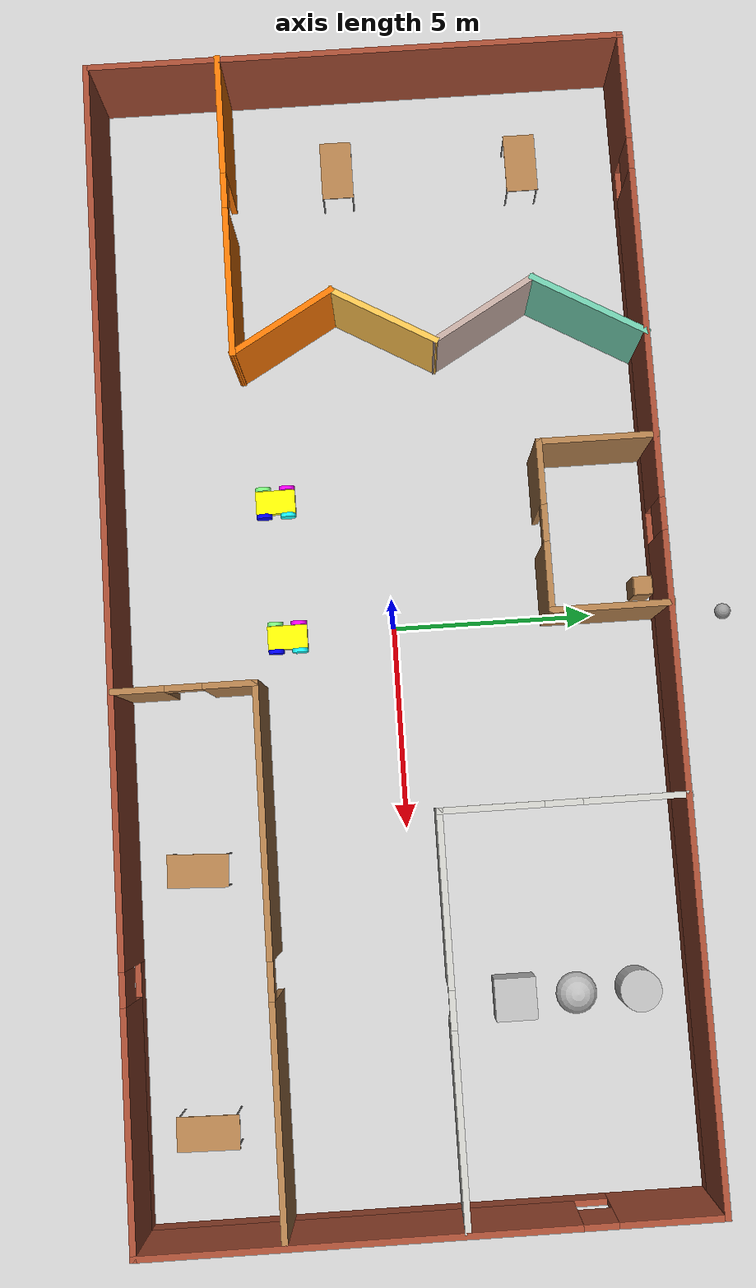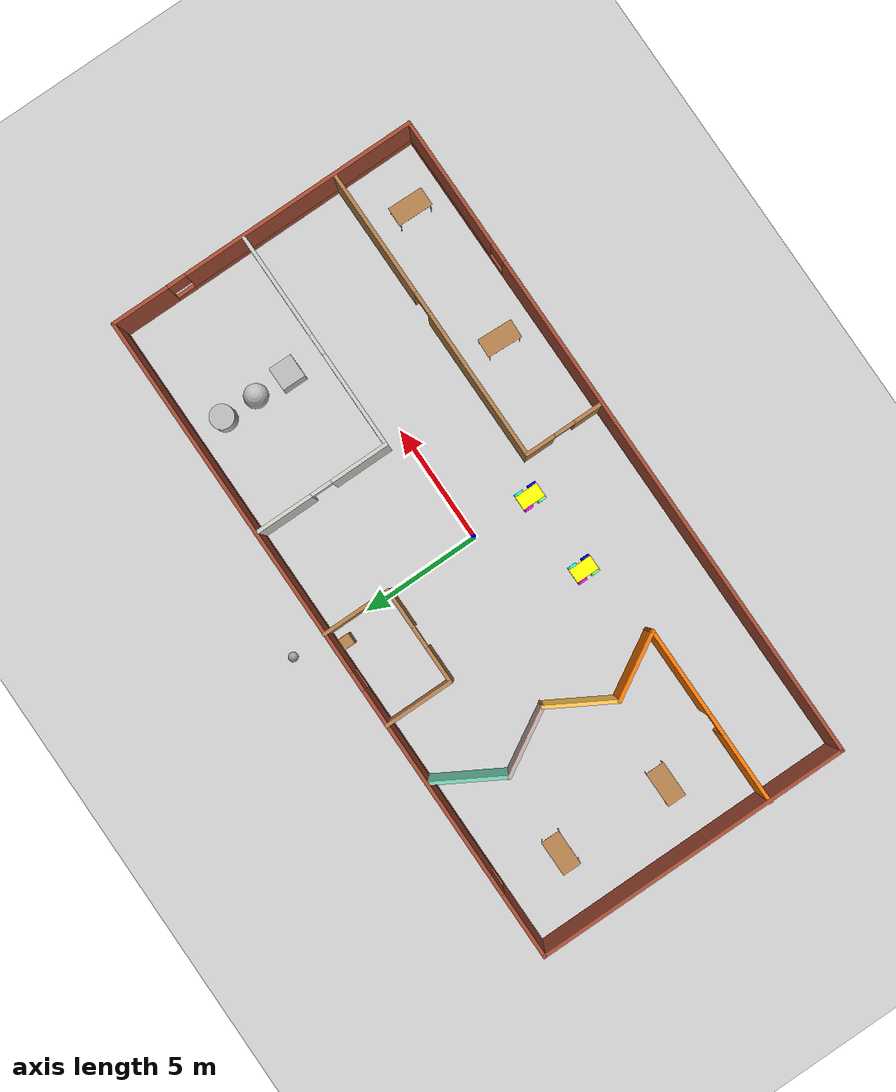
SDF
<sdf version="1.6">
 <world name="default">
  <light name="sun" type="directional">
   <pose>0 0 10 0 -0 0</pose>
   <diffuse>0.8 0.8 0.8 1</diffuse>
   <specular>0.2 0.2 0.2 1</specular>
   <attenuation>
    <range>1000</range>
    <constant>0.9</constant>
    <linear>0.01</linear>
    <quadratic>0.001</quadratic>
   </attenuation>
   <direction>-0.5 0.1 -0.9</direction>
  </light>
  <model name="ground_plane">
   <static>1</static>
   <link name="link">
    <collision name="collision">
     <geometry><plane><normal>0 0 1</normal><size>100 100</size></plane></geometry>
     <surface>
      <contact><collide_bitmask>65535</collide_bitmask></contact>
      <friction><ode><mu>100</mu><mu2>50</mu2></ode></friction>
     </surface>
    </collision>
    <visual name="visual">
     <cast_shadows>0</cast_shadows>
     <geometry><plane><normal>0 0 1</normal><size>100 100</size></plane></geometry>
     <material>
      <script><uri>file://media/materials/scripts/gazebo.material</uri><name>Gazebo/Grey</name></script>
     </material>
    </visual>
   </link>
  </model>
  <gravity>0 0 -9.8</gravity>
  <magnetic_field>6e-06 2.3e-05 -4.2e-05</magnetic_field>
  <atmosphere type="adiabatic"/>
  <physics name="default_physics" default="0" type="ode">
   <max_step_size>0.001</max_step_size>
   <real_time_factor>1</real_time_factor>
   <real_time_update_rate>1000</real_time_update_rate>
  </physics>
  <scene><ambient>0.4 0.4 0.4 1</ambient><background>0.7 0.7 0.7 1</background><shadows>1</shadows></scene>
  <spherical_coordinates>
   <surface_model>EARTH_WGS84</surface_model>
   <latitude_deg>0</latitude_deg>
   <longitude_deg>0</longitude_deg>
   <elevation>0</elevation>
   <heading_deg>0</heading_deg>
  </spherical_coordinates>
  <model name="office">
   <pose>-0.0877 -0.031287 0 0 -0 0</pose>
   <link name="Wall_0">
    <collision name="Wall_0_Collision">
     <geometry><box><size>13.5 0.15 2.5</size></box></geometry>
     <pose>0 0 1.25 0 -0 0</pose>
    </collision>
    <visual name="Wall_0_Visual">
     <pose>0 0 1.25 0 -0 0</pose>
     <geometry><box><size>13.5 0.15 2.5</size></box></geometry>
     <material>
      <script><uri>file://media/materials/scripts/gazebo.material</uri><name>Gazebo/Bricks</name></script>
      <ambient>1 1 1 1</ambient>
     </material>
     <meta><layer>0</layer></meta>
    </visual>
    <pose>-14.1592 -0.021409 0 0 0 -1.5708</pose>
   </link>
   <link name="Wall_1">
    <pose>0.015849 -6.69641 0 0 -0 0</pose>
    <visual name="Wall_1_Visual_0">
     <pose>-3.18138 0 1.25 0 -0 0</pose>
     <geometry><box><size>22.1372 0.15 2.5</size></box></geometry>
     <material>
      <script><uri>file://media/materials/scripts/gazebo.material</uri><name>Gazebo/Bricks</name></script>
      <ambient>1 1 1 1</ambient>
     </material>
     <meta><layer>0</layer></meta>
    </visual>
    <collision name="Wall_1_Collision_0">
     <geometry><box><size>22.1372 0.15 2.5</size></box></geometry>
     <pose>-3.18138 0 1.25 0 -0 0</pose>
    </collision>
    <visual name="Wall_1_Visual_1">
     <pose>11.0686 0 0.25 0 -0 0</pose>
     <geometry><box><size>6.36277 0.15 0.5</size></box></geometry>
     <material>
      <script><uri>file://media/materials/scripts/gazebo.material</uri><name>Gazebo/Bricks</name></script>
      <ambient>1 1 1 1</ambient>
     </material>
     <meta><layer>0</layer></meta>
    </visual>
    <collision name="Wall_1_Collision_1">
     <geometry><box><size>6.36277 0.15 0.5</size></box></geometry>
     <pose>11.0686 0 0.25 0 -0 0</pose>
    </collision>
    <visual name="Wall_1_Visual_2">
     <pose>11.4686 0 1.5 0 -0 0</pose>
     <geometry><box><size>5.56277 0.15 2</size></box></geometry>
     <material>
      <script><uri>file://media/materials/scripts/gazebo.material</uri><name>Gazebo/Bricks</name></script>
      <ambient>1 1 1 1</ambient>
     </material>
     <meta><layer>0</layer></meta>
    </visual>
    <collision name="Wall_1_Collision_2">
     <geometry><box><size>5.56277 0.15 2</size></box></geometry>
     <pose>11.4686 0 1.5 0 -0 0</pose>
    </collision>
    <visual name="Wall_1_Visual_3">
     <pose>8.28723 0 1.9 0 -0 0</pose>
     <geometry><box><size>0.8 0.15 1.2</size></box></geometry>
     <material>
      <script><uri>file://media/materials/scripts/gazebo.material</uri><name>Gazebo/Bricks</name></script>
      <ambient>1 1 1 1</ambient>
     </material>
     <meta><layer>0</layer></meta>
    </visual>
    <collision name="Wall_1_Collision_3">
     <geometry><box><size>0.8 0.15 1.2</size></box></geometry>
     <pose>8.28723 0 1.9 0 -0 0</pose>
    </collision>
   </link>
   <link name="Wall_10">
    <collision name="Wall_10_Collision">
     <geometry><box><size>3 0.15 2.5</size></box></geometry>
     <pose>0 0 1.25 0 -0 0</pose>
    </collision>
    <visual name="Wall_10_Visual">
     <pose>0 0 1.25 0 -0 0</pose>
     <geometry><box><size>3 0.15 2.5</size></box></geometry>
     <material>
      <script><uri>file://media/materials/scripts/gazebo.material</uri><name>Gazebo/Grey</name></script>
      <ambient>0.760784 0.662745 0.627451 1</ambient>
     </material>
     <meta><layer>0</layer></meta>
    </visual>
    <pose>-7.30335 2.75019 0 0 0 -1.0472</pose>
   </link>
   <link name="Wall_11">
    <collision name="Wall_11_Collision">
     <geometry><box><size>3 0.15 2.5</size></box></geometry>
     <pose>0 0 1.25 0 -0 0</pose>
    </collision>
    <visual name="Wall_11_Visual">
     <pose>0 0 1.25 0 -0 0</pose>
     <geometry><box><size>3 0.15 2.5</size></box></geometry>
     <material>
      <script><uri>file://media/materials/scripts/gazebo.material</uri><name>Gazebo/Grey</name></script>
      <ambient>1 0.764706 0.305882 1</ambient>
     </material>
     <meta><layer>0</layer></meta>
    </visual>
    <pose>-7.30335 0.282021 0 0 0 -2.0944</pose>
   </link>
   <link name="Wall_12">
    <collision name="Wall_12_Collision">
     <geometry><box><size>3 0.15 2.5</size></box></geometry>
     <pose>0 0 1.25 0 -0 0</pose>
    </collision>
    <visual name="Wall_12_Visual">
     <pose>0 0 1.25 0 -0 0</pose>
     <geometry><box><size>3 0.15 2.5</size></box></geometry>
     <material>
      <script><uri>file://media/materials/scripts/gazebo.material</uri><name>Gazebo/Grey</name></script>
      <ambient>0.996078 0.47451 0.0196078 1</ambient>
     </material>
     <meta><layer>0</layer></meta>
    </visual>
    <pose>-7.30335 -2.18615 0 0 0 -1.0472</pose>
   </link>
   <link name="Wall_13">
    <pose>-10.3909 -3.42024 0 0 -0 3.14159</pose>
    <visual name="Wall_13_Visual_0">
     <pose>-1.98848 0 1.25 0 -0 0</pose>
     <geometry><box><size>3.77303 0.15 2.5</size></box></geometry>
     <material>
      <script><uri>file://media/materials/scripts/gazebo.material</uri><name>Gazebo/Grey</name></script>
      <ambient>0.996078 0.47451 0.0196078 1</ambient>
     </material>
     <meta><layer>0</layer></meta>
    </visual>
    <collision name="Wall_13_Collision_0">
     <geometry><box><size>3.77303 0.15 2.5</size></box></geometry>
     <pose>-1.98848 0 1.25 0 -0 0</pose>
    </collision>
    <visual name="Wall_13_Visual_1">
     <pose>2.33652 0 1.25 0 -0 0</pose>
     <geometry><box><size>3.07697 0.15 2.5</size></box></geometry>
     <material>
      <script><uri>file://media/materials/scripts/gazebo.material</uri><name>Gazebo/Grey</name></script>
      <ambient>0.996078 0.47451 0.0196078 1</ambient>
     </material>
     <meta><layer>0</layer></meta>
    </visual>
    <collision name="Wall_13_Collision_1">
     <geometry><box><size>3.07697 0.15 2.5</size></box></geometry>
     <pose>2.33652 0 1.25 0 -0 0</pose>
    </collision>
    <visual name="Wall_13_Visual_2">
     <pose>0.348034 0 2.25 0 -0 0</pose>
     <geometry><box><size>0.9 0.15 0.5</size></box></geometry>
     <material>
      <script><uri>file://media/materials/scripts/gazebo.material</uri><name>Gazebo/Grey</name></script>
      <ambient>0.996078 0.47451 0.0196078 1</ambient>
     </material>
     <meta><layer>0</layer></meta>
    </visual>
    <collision name="Wall_13_Collision_2">
     <geometry><box><size>0.9 0.15 0.5</size></box></geometry>
     <pose>0.348034 0 2.25 0 -0 0</pose>
    </collision>
   </link>
   <link name="Wall_15">
    <pose>4.73531 3.74396 0 0 0 -1.5708</pose>
    <visual name="Wall_15_Visual_0">
     <pose>-1.71476 0 1.25 0 -0 0</pose>
     <geometry><box><size>2.57049 0.15 2.5</size></box></geometry>
     <material>
      <script><uri>file://media/materials/scripts/gazebo.material</uri><name>Gazebo/CeilingTiled</name></script>
      <ambient>1 1 1 1</ambient>
     </material>
     <meta><layer>0</layer></meta>
    </visual>
    <collision name="Wall_15_Collision_0">
     <geometry><box><size>2.57049 0.15 2.5</size></box></geometry>
     <pose>-1.71476 0 1.25 0 -0 0</pose>
    </collision>
    <visual name="Wall_15_Visual_1">
     <pose>1.73524 0 1.25 0 -0 0</pose>
     <geometry><box><size>2.52951 0.15 2.5</size></box></geometry>
     <material>
      <script><uri>file://media/materials/scripts/gazebo.material</uri><name>Gazebo/CeilingTiled</name></script>
      <ambient>1 1 1 1</ambient>
     </material>
     <meta><layer>0</layer></meta>
    </visual>
    <collision name="Wall_15_Collision_1">
     <geometry><box><size>2.52951 0.15 2.5</size></box></geometry>
     <pose>1.73524 0 1.25 0 -0 0</pose>
    </collision>
    <visual name="Wall_15_Visual_2">
     <pose>0.020489 0 2.25 0 -0 0</pose>
     <geometry><box><size>0.9 0.15 0.5</size></box></geometry>
     <material>
      <script><uri>file://media/materials/scripts/gazebo.material</uri><name>Gazebo/CeilingTiled</name></script>
      <ambient>1 1 1 1</ambient>
     </material>
     <meta><layer>0</layer></meta>
    </visual>
    <collision name="Wall_15_Collision_2">
     <geometry><box><size>0.9 0.15 0.5</size></box></geometry>
     <pose>0.020489 0 2.25 0 -0 0</pose>
    </collision>
   </link>
   <link name="Wall_16">
    <pose>9.41031 0.818959 0 0 -0 0</pose>
    <visual name="Wall_16_Visual_0">
     <pose>-2.67653 0 1.25 0 -0 0</pose>
     <geometry><box><size>4.14695 0.15 2.5</size></box></geometry>
     <material>
      <script><uri>file://media/materials/scripts/gazebo.material</uri><name>Gazebo/CeilingTiled</name></script>
      <ambient>1 1 1 1</ambient>
     </material>
     <meta><layer>0</layer></meta>
    </visual>
    <collision name="Wall_16_Collision_0">
     <geometry><box><size>4.14695 0.15 2.5</size></box></geometry>
     <pose>-2.67653 0 1.25 0 -0 0</pose>
    </collision>
    <visual name="Wall_16_Visual_1">
     <pose>2.52347 0 1.25 0 -0 0</pose>
     <geometry><box><size>4.45305 0.15 2.5</size></box></geometry>
     <material>
      <script><uri>file://media/materials/scripts/gazebo.material</uri><name>Gazebo/CeilingTiled</name></script>
      <ambient>1 1 1 1</ambient>
     </material>
     <meta><layer>0</layer></meta>
    </visual>
    <collision name="Wall_16_Collision_1">
     <geometry><box><size>4.45305 0.15 2.5</size></box></geometry>
     <pose>2.52347 0 1.25 0 -0 0</pose>
    </collision>
    <visual name="Wall_16_Visual_2">
     <pose>-0.153052 0 2.25 0 -0 0</pose>
     <geometry><box><size>0.9 0.15 0.5</size></box></geometry>
     <material>
      <script><uri>file://media/materials/scripts/gazebo.material</uri><name>Gazebo/CeilingTiled</name></script>
      <ambient>1 1 1 1</ambient>
     </material>
     <meta><layer>0</layer></meta>
    </visual>
    <collision name="Wall_16_Collision_2">
     <geometry><box><size>0.9 0.15 0.5</size></box></geometry>
     <pose>-0.153052 0 2.25 0 -0 0</pose>
    </collision>
   </link>
   <link name="Wall_18">
    <pose>1.45793 -4.97297 0 0 -0 1.5708</pose>
    <visual name="Wall_18_Visual_0">
     <pose>-1.10779 0 1.25 0 -0 0</pose>
     <geometry><box><size>1.28443 0.15 2.5</size></box></geometry>
     <material>
      <script><uri>file://media/materials/scripts/gazebo.material</uri><name>Gazebo/Wood</name></script>
      <ambient>1 1 1 1</ambient>
     </material>
     <meta><layer>0</layer></meta>
    </visual>
    <collision name="Wall_18_Collision_0">
     <geometry><box><size>1.28443 0.15 2.5</size></box></geometry>
     <pose>-1.10779 0 1.25 0 -0 0</pose>
    </collision>
    <visual name="Wall_18_Visual_1">
     <pose>1.09221 0 1.25 0 -0 0</pose>
     <geometry><box><size>1.31557 0.15 2.5</size></box></geometry>
     <material>
      <script><uri>file://media/materials/scripts/gazebo.material</uri><name>Gazebo/Wood</name></script>
      <ambient>1 1 1 1</ambient>
     </material>
     <meta><layer>0</layer></meta>
    </visual>
    <collision name="Wall_18_Collision_1">
     <geometry><box><size>1.31557 0.15 2.5</size></box></geometry>
     <pose>1.09221 0 1.25 0 -0 0</pose>
    </collision>
    <visual name="Wall_18_Visual_2">
     <pose>-0.01557 0 2.25 0 -0 0</pose>
     <geometry><box><size>0.9 0.15 0.5</size></box></geometry>
     <material>
      <script><uri>file://media/materials/scripts/gazebo.material</uri><name>Gazebo/Wood</name></script>
      <ambient>1 1 1 1</ambient>
     </material>
     <meta><layer>0</layer></meta>
    </visual>
    <collision name="Wall_18_Collision_2">
     <geometry><box><size>0.9 0.15 0.5</size></box></geometry>
     <pose>-0.01557 0 2.25 0 -0 0</pose>
    </collision>
   </link>
   <link name="Wall_19">
    <pose>7.75793 -3.29797 0 0 -0 0</pose>
    <visual name="Wall_19_Visual_0">
     <pose>-3.11918 0 1.25 0 -0 0</pose>
     <geometry><box><size>6.51164 0.15 2.5</size></box></geometry>
     <material>
      <script><uri>file://media/materials/scripts/gazebo.material</uri><name>Gazebo/Wood</name></script>
      <ambient>1 1 1 1</ambient>
     </material>
     <meta><layer>0</layer></meta>
    </visual>
    <collision name="Wall_19_Collision_0">
     <geometry><box><size>6.51164 0.15 2.5</size></box></geometry>
     <pose>-3.11918 0 1.25 0 -0 0</pose>
    </collision>
    <visual name="Wall_19_Visual_1">
     <pose>3.70582 0 1.25 0 -0 0</pose>
     <geometry><box><size>5.33836 0.15 2.5</size></box></geometry>
     <material>
      <script><uri>file://media/materials/scripts/gazebo.material</uri><name>Gazebo/Wood</name></script>
      <ambient>1 1 1 1</ambient>
     </material>
     <meta><layer>0</layer></meta>
    </visual>
    <collision name="Wall_19_Collision_1">
     <geometry><box><size>5.33836 0.15 2.5</size></box></geometry>
     <pose>3.70582 0 1.25 0 -0 0</pose>
    </collision>
    <visual name="Wall_19_Visual_2">
     <pose>0.586637 0 2.25 0 -0 0</pose>
     <geometry><box><size>0.9 0.15 0.5</size></box></geometry>
     <material>
      <script><uri>file://media/materials/scripts/gazebo.material</uri><name>Gazebo/Wood</name></script>
      <ambient>1 1 1 1</ambient>
     </material>
     <meta><layer>0</layer></meta>
    </visual>
    <collision name="Wall_19_Collision_2">
     <geometry><box><size>0.9 0.15 0.5</size></box></geometry>
     <pose>0.586637 0 2.25 0 -0 0</pose>
    </collision>
   </link>
   <link name="Wall_22">
    <collision name="Wall_22_Collision">
     <geometry><box><size>3 0.15 2.5</size></box></geometry>
     <pose>0 0 1.25 0 -0 0</pose>
    </collision>
    <visual name="Wall_22_Visual">
     <pose>0 0 1.25 0 -0 0</pose>
     <geometry><box><size>3 0.15 2.5</size></box></geometry>
     <material>
      <script><uri>file://media/materials/scripts/gazebo.material</uri><name>Gazebo/Wood</name></script>
      <ambient>1 1 1 1</ambient>
     </material>
     <meta><layer>0</layer></meta>
    </visual>
    <pose>-3.89373 5.24396 0 0 0 -1.5708</pose>
   </link>
   <link name="Wall_23">
    <pose>-1.84373 3.81896 0 0 -0 0</pose>
    <visual name="Wall_23_Visual_0">
     <pose>-1.31684 0 1.25 0 -0 0</pose>
     <geometry><box><size>1.61632 0.15 2.5</size></box></geometry>
     <material>
      <script><uri>file://media/materials/scripts/gazebo.material</uri><name>Gazebo/Wood</name></script>
      <ambient>1 1 1 1</ambient>
     </material>
     <meta><layer>0</layer></meta>
    </visual>
    <collision name="Wall_23_Collision_0">
     <geometry><box><size>1.61632 0.15 2.5</size></box></geometry>
     <pose>-1.31684 0 1.25 0 -0 0</pose>
    </collision>
    <visual name="Wall_23_Visual_1">
     <pose>1.25816 0 1.25 0 -0 0</pose>
     <geometry><box><size>1.73368 0.15 2.5</size></box></geometry>
     <material>
      <script><uri>file://media/materials/scripts/gazebo.material</uri><name>Gazebo/Wood</name></script>
      <ambient>1 1 1 1</ambient>
     </material>
     <meta><layer>0</layer></meta>
    </visual>
    <collision name="Wall_23_Collision_1">
     <geometry><box><size>1.73368 0.15 2.5</size></box></geometry>
     <pose>1.25816 0 1.25 0 -0 0</pose>
    </collision>
    <visual name="Wall_23_Visual_2">
     <pose>-0.058683 0 2.25 0 -0 0</pose>
     <geometry><box><size>0.9 0.15 0.5</size></box></geometry>
     <material>
      <script><uri>file://media/materials/scripts/gazebo.material</uri><name>Gazebo/Wood</name></script>
      <ambient>1 1 1 1</ambient>
     </material>
     <meta><layer>0</layer></meta>
    </visual>
    <collision name="Wall_23_Collision_2">
     <geometry><box><size>0.9 0.15 0.5</size></box></geometry>
     <pose>-0.058683 0 2.25 0 -0 0</pose>
    </collision>
   </link>
   <link name="Wall_24">
    <collision name="Wall_24_Collision">
     <geometry><box><size>3 0.15 2.5</size></box></geometry>
     <pose>0 0 1.25 0 -0 0</pose>
    </collision>
    <visual name="Wall_24_Visual">
     <pose>0 0 1.25 0 -0 0</pose>
     <geometry><box><size>3 0.15 2.5</size></box></geometry>
     <material>
      <script><uri>file://media/materials/scripts/gazebo.material</uri><name>Gazebo/Wood</name></script>
      <ambient>1 1 1 1</ambient>
     </material>
     <meta><layer>0</layer></meta>
    </visual>
    <pose>0.206268 5.24396 0 0 -0 1.5708</pose>
   </link>
   <link name="Wall_5">
    <pose>0.015849 6.65359 0 0 -0 0</pose>
    <visual name="Wall_5_Visual_0">
     <pose>-12.8476 0 1.25 0 -0 0</pose>
     <geometry><box><size>2.80487 0.15 2.5</size></box></geometry>
     <material>
      <script><uri>file://media/materials/scripts/gazebo.material</uri><name>Gazebo/Bricks</name></script>
      <ambient>1 1 1 1</ambient>
     </material>
     <meta><layer>0</layer></meta>
    </visual>
    <collision name="Wall_5_Collision_0">
     <geometry><box><size>2.80487 0.15 2.5</size></box></geometry>
     <pose>-12.8476 0 1.25 0 -0 0</pose>
    </collision>
    <visual name="Wall_5_Visual_1">
     <pose>1.40243 0 0.25 0 -0 0</pose>
     <geometry><box><size>25.6951 0.15 0.5</size></box></geometry>
     <material>
      <script><uri>file://media/materials/scripts/gazebo.material</uri><name>Gazebo/Bricks</name></script>
      <ambient>1 1 1 1</ambient>
     </material>
     <meta><layer>0</layer></meta>
    </visual>
    <collision name="Wall_5_Collision_1">
     <geometry><box><size>25.6951 0.15 0.5</size></box></geometry>
     <pose>1.40243 0 0.25 0 -0 0</pose>
    </collision>
    <visual name="Wall_5_Visual_2">
     <pose>-6.50244 0 1.5 0 -0 0</pose>
     <geometry><box><size>8.28538 0.15 2</size></box></geometry>
     <material>
      <script><uri>file://media/materials/scripts/gazebo.material</uri><name>Gazebo/Bricks</name></script>
      <ambient>1 1 1 1</ambient>
     </material>
     <meta><layer>0</layer></meta>
    </visual>
    <collision name="Wall_5_Collision_2">
     <geometry><box><size>8.28538 0.15 2</size></box></geometry>
     <pose>-6.50244 0 1.5 0 -0 0</pose>
    </collision>
    <visual name="Wall_5_Visual_3">
     <pose>6.34513 0 1.5 0 -0 0</pose>
     <geometry><box><size>15.8097 0.15 2</size></box></geometry>
     <material>
      <script><uri>file://media/materials/scripts/gazebo.material</uri><name>Gazebo/Bricks</name></script>
      <ambient>1 1 1 1</ambient>
     </material>
     <meta><layer>0</layer></meta>
    </visual>
    <collision name="Wall_5_Collision_3">
     <geometry><box><size>15.8097 0.15 2</size></box></geometry>
     <pose>6.34513 0 1.5 0 -0 0</pose>
    </collision>
    <visual name="Wall_5_Visual_4">
     <pose>-11.0451 0 1.9 0 -0 0</pose>
     <geometry><box><size>0.8 0.15 1.2</size></box></geometry>
     <material>
      <script><uri>file://media/materials/scripts/gazebo.material</uri><name>Gazebo/Bricks</name></script>
      <ambient>1 1 1 1</ambient>
     </material>
     <meta><layer>0</layer></meta>
    </visual>
    <collision name="Wall_5_Collision_4">
     <geometry><box><size>0.8 0.15 1.2</size></box></geometry>
     <pose>-11.0451 0 1.9 0 -0 0</pose>
    </collision>
    <visual name="Wall_5_Visual_5">
     <pose>-1.95975 0 1.9 0 -0 0</pose>
     <geometry><box><size>0.8 0.15 1.2</size></box></geometry>
     <material>
      <script><uri>file://media/materials/scripts/gazebo.material</uri><name>Gazebo/Bricks</name></script>
      <ambient>1 1 1 1</ambient>
     </material>
     <meta><layer>0</layer></meta>
    </visual>
    <collision name="Wall_5_Collision_5">
     <geometry><box><size>0.8 0.15 1.2</size></box></geometry>
     <pose>-1.95975 0 1.9 0 -0 0</pose>
    </collision>
   </link>
   <link name="Wall_6">
    <pose>14.1908 -0.021409 0 0 0 -1.5708</pose>
    <visual name="Wall_6_Visual_0">
     <pose>-5.48893 0 1.25 0 -0 0</pose>
     <geometry><box><size>2.52215 0.15 2.5</size></box></geometry>
     <material>
      <script><uri>file://media/materials/scripts/gazebo.material</uri><name>Gazebo/Bricks</name></script>
      <ambient>1 1 1 1</ambient>
     </material>
     <meta><layer>0</layer></meta>
    </visual>
    <collision name="Wall_6_Collision_0">
     <geometry><box><size>2.52215 0.15 2.5</size></box></geometry>
     <pose>-5.48893 0 1.25 0 -0 0</pose>
    </collision>
    <visual name="Wall_6_Visual_1">
     <pose>1.26107 0 0.25 0 -0 0</pose>
     <geometry><box><size>10.9779 0.15 0.5</size></box></geometry>
     <material>
      <script><uri>file://media/materials/scripts/gazebo.material</uri><name>Gazebo/Bricks</name></script>
      <ambient>1 1 1 1</ambient>
     </material>
     <meta><layer>0</layer></meta>
    </visual>
    <collision name="Wall_6_Collision_1">
     <geometry><box><size>10.9779 0.15 0.5</size></box></geometry>
     <pose>1.26107 0 0.25 0 -0 0</pose>
    </collision>
    <visual name="Wall_6_Visual_2">
     <pose>1.66108 0 1.5 0 -0 0</pose>
     <geometry><box><size>10.1778 0.15 2</size></box></geometry>
     <material>
      <script><uri>file://media/materials/scripts/gazebo.material</uri><name>Gazebo/Bricks</name></script>
      <ambient>1 1 1 1</ambient>
     </material>
     <meta><layer>0</layer></meta>
    </visual>
    <collision name="Wall_6_Collision_2">
     <geometry><box><size>10.1778 0.15 2</size></box></geometry>
     <pose>1.66108 0 1.5 0 -0 0</pose>
    </collision>
    <visual name="Wall_6_Visual_3">
     <pose>-3.82785 0 1.9 0 -0 0</pose>
     <geometry><box><size>0.8 0.15 1.2</size></box></geometry>
     <material>
      <script><uri>file://media/materials/scripts/gazebo.material</uri><name>Gazebo/Bricks</name></script>
      <ambient>1 1 1 1</ambient>
     </material>
     <meta><layer>0</layer></meta>
    </visual>
    <collision name="Wall_6_Collision_3">
     <geometry><box><size>0.8 0.15 1.2</size></box></geometry>
     <pose>-3.82785 0 1.9 0 -0 0</pose>
    </collision>
   </link>
   <link name="Wall_9">
    <collision name="Wall_9_Collision">
     <geometry><box><size>3.25 0.15 2.5</size></box></geometry>
     <pose>0 0 1.25 0 -0 0</pose>
    </collision>
    <visual name="Wall_9_Visual">
     <pose>0 0 1.25 0 -0 0</pose>
     <geometry><box><size>3.25 0.15 2.5</size></box></geometry>
     <material>
      <script><uri>file://media/materials/scripts/gazebo.material</uri><name>Gazebo/Grey</name></script>
      <ambient>0.435294 0.796078 0.67451 1</ambient>
     </material>
     <meta><layer>0</layer></meta>
    </visual>
    <pose>-7.24085 5.32662 0 0 0 -2.0944</pose>
   </link>
   <static>1</static>
  </model>
  <model name="cabinet">
   <static>1</static>
   <link name="cabinet_bottom_plate">
    <inertial>
     <pose>0 0 -1 0 -0 0</pose>
     <inertia><ixx>2.05</ixx><ixy>0</ixy><ixz>0</ixz><iyy>2.05</iyy><iyz>0</iyz><izz>2.05</izz></inertia>
     <mass>25</mass>
    </inertial>
    <collision name="cabinet_bottom_plate_geom">
     <pose>0 0 0.01 0 -0 0</pose>
     <geometry><box><size>0.45 0.45 0.02</size></box></geometry>
    </collision>
    <visual name="cabinet_bottom_plate_geom_visual">
     <pose>0 0 0.01 0 -0 0</pose>
     <geometry><box><size>0.45 0.45 0.02</size></box></geometry>
     <material>
      <script><uri>file://media/materials/scripts/gazebo.material</uri><name>Gazebo/Wood</name></script>
     </material>
    </visual>
    <collision name="cabinet_bottom_plate_geom_cabinet_back_plate">
     <pose>0.235 0 0.51 0 -0 0</pose>
     <geometry><box><size>0.02 0.45 1.02</size></box></geometry>
    </collision>
    <visual name="cabinet_bottom_plate_geom_cabinet_back_plate_visual">
     <pose>0.235 0 0.51 0 -0 0</pose>
     <geometry><box><size>0.02 0.45 1.02</size></box></geometry>
     <material>
      <script><uri>file://media/materials/scripts/gazebo.material</uri><name>Gazebo/Wood</name></script>
     </material>
    </visual>
    <collision name="cabinet_bottom_plate_geom_cabinet_left_plate">
     <pose>0 0.235 0.51 0 -0 0</pose>
     <geometry><box><size>0.45 0.02 1.02</size></box></geometry>
    </collision>
    <visual name="cabinet_bottom_plate_geom_cabinet_left_plate_visual">
     <pose>0 0.235 0.51 0 -0 0</pose>
     <geometry><box><size>0.45 0.02 1.02</size></box></geometry>
     <material>
      <script><uri>file://media/materials/scripts/gazebo.material</uri><name>Gazebo/Wood</name></script>
     </material>
    </visual>
    <collision name="cabinet_bottom_plate_geom_cabinet_middle_plate">
     <pose>0 0 0.51 0 -0 0</pose>
     <geometry><box><size>0.45 0.45 0.02</size></box></geometry>
    </collision>
    <visual name="cabinet_bottom_plate_geom_cabinet_middle_plate_visual">
     <pose>0 0 0.51 0 -0 0</pose>
     <geometry><box><size>0.45 0.45 0.02</size></box></geometry>
     <material>
      <script><uri>file://media/materials/scripts/gazebo.material</uri><name>Gazebo/Wood</name></script>
     </material>
    </visual>
    <collision name="cabinet_bottom_plate_geom_cabinet_right_plate">
     <pose>0 -0.235 0.51 0 -0 0</pose>
     <geometry><box><size>0.45 0.02 1.02</size></box></geometry>
    </collision>
    <visual name="cabinet_bottom_plate_geom_cabinet_right_plate_visual">
     <pose>0 -0.235 0.51 0 -0 0</pose>
     <geometry><box><size>0.45 0.02 1.02</size></box></geometry>
     <material>
      <script><uri>file://media/materials/scripts/gazebo.material</uri><name>Gazebo/Wood</name></script>
     </material>
    </visual>
    <collision name="cabinet_bottom_plate_geom_cabinet_top_plate">
     <pose>0 0 1.01 0 -0 0</pose>
     <geometry><box><size>0.45 0.45 0.02</size></box></geometry>
    </collision>
    <visual name="cabinet_bottom_plate_geom_cabinet_top_plate_visual">
     <pose>0 0 1.01 0 -0 0</pose>
     <geometry><box><size>0.45 0.45 0.02</size></box></geometry>
     <material>
      <script><uri>file://media/materials/scripts/gazebo.material</uri><name>Gazebo/Wood</name></script>
     </material>
    </visual>
   </link>
   <pose>-0.545344 6.23489 0 0 -0 0</pose>
  </model>
  <model name="table">
   <static>1</static>
   <link name="link">
    <collision name="surface">
     <pose>0 0 1 0 -0 0</pose>
     <geometry><box><size>1.5 0.8 0.03</size></box></geometry>
     <surface><friction><ode><mu>0.6</mu><mu2>0.6</mu2></ode></friction></surface>
    </collision>
    <visual name="visual1">
     <pose>0 0 1 0 -0 0</pose>
     <geometry><box><size>1.5 0.8 0.03</size></box></geometry>
     <material>
      <script><uri>file://media/materials/scripts/gazebo.material</uri><name>Gazebo/Wood</name></script>
     </material>
    </visual>
    <collision name="front_left_leg">
     <pose>0.68 0.38 0.5 0 -0 0</pose>
     <geometry><cylinder><radius>0.02</radius><length>1</length></cylinder></geometry>
    </collision>
    <visual name="front_left_leg">
     <pose>0.68 0.38 0.5 0 -0 0</pose>
     <geometry><cylinder><radius>0.02</radius><length>1</length></cylinder></geometry>
     <material>
      <script><uri>file://media/materials/scripts/gazebo.material</uri><name>Gazebo/Grey</name></script>
     </material>
    </visual>
    <collision name="front_right_leg">
     <pose>0.68 -0.38 0.5 0 -0 0</pose>
     <geometry><cylinder><radius>0.02</radius><length>1</length></cylinder></geometry>
    </collision>
    <visual name="front_right_leg">
     <pose>0.68 -0.38 0.5 0 -0 0</pose>
     <geometry><cylinder><radius>0.02</radius><length>1</length></cylinder></geometry>
     <material>
      <script><uri>file://media/materials/scripts/gazebo.material</uri><name>Gazebo/Grey</name></script>
     </material>
    </visual>
    <collision name="back_right_leg">
     <pose>-0.68 -0.38 0.5 0 -0 0</pose>
     <geometry><cylinder><radius>0.02</radius><length>1</length></cylinder></geometry>
    </collision>
    <visual name="back_right_leg">
     <pose>-0.68 -0.38 0.5 0 -0 0</pose>
     <geometry><cylinder><radius>0.02</radius><length>1</length></cylinder></geometry>
     <material>
      <script><uri>file://media/materials/scripts/gazebo.material</uri><name>Gazebo/Grey</name></script>
     </material>
    </visual>
    <collision name="back_left_leg">
     <pose>-0.68 0.38 0.5 0 -0 0</pose>
     <geometry><cylinder><radius>0.02</radius><length>1</length></cylinder></geometry>
    </collision>
    <visual name="back_left_leg">
     <pose>-0.68 0.38 0.5 0 -0 0</pose>
     <geometry><cylinder><radius>0.02</radius><length>1</length></cylinder></geometry>
     <material>
      <script><uri>file://media/materials/scripts/gazebo.material</uri><name>Gazebo/Grey</name></script>
     </material>
    </visual>
   </link>
   <pose>-11.7268 4.05281 0 0 -0 0</pose>
  </model>
  <model name="textured_shapes">
   <pose>9.21864 3.83776 0.5 0 -0 0</pose>
   <link name="box">
    <pose>0 -1.5 0 0 -0 0</pose>
    <collision name="collision"><geometry><box><size>1 1 1</size></box></geometry></collision>
    <visual name="visual">
     <geometry><box><size>1 1 1</size></box></geometry>
     <material>
      <script>
       <uri>model://textured_shapes/materials/scripts</uri>
       <uri>model://textured_shapes/materials/textures</uri>
       <name>TexturedShape/Squares</name>
      </script>
     </material>
    </visual>
    <inertial>
     <inertia><ixx>1</ixx><ixy>0</ixy><ixz>0</ixz><iyy>1</iyy><iyz>0</iyz><izz>1</izz></inertia>
     <mass>1</mass>
    </inertial>
   </link>
   <link name="sphere">
    <collision name="collision"><geometry><sphere><radius>0.5</radius></sphere></geometry></collision>
    <visual name="visual">
     <geometry><sphere><radius>0.5</radius></sphere></geometry>
     <material>
      <script>
       <uri>model://textured_shapes/materials/scripts</uri>
       <uri>model://textured_shapes/materials/textures</uri>
       <name>TexturedShape/Squares</name>
      </script>
     </material>
    </visual>
    <inertial>
     <inertia><ixx>1</ixx><ixy>0</ixy><ixz>0</ixz><iyy>1</iyy><iyz>0</iyz><izz>1</izz></inertia>
     <mass>1</mass>
    </inertial>
   </link>
   <link name="cylinder">
    <pose>0 1.5 0 0 -0 0</pose>
    <collision name="collision">
     <geometry><cylinder><radius>0.5</radius><length>1</length></cylinder></geometry>
    </collision>
    <visual name="visual">
     <geometry><cylinder><radius>0.5</radius><length>1</length></cylinder></geometry>
     <material>
      <script>
       <uri>model://textured_shapes/materials/scripts</uri>
       <uri>model://textured_shapes/materials/textures</uri>
       <name>TexturedShape/Squares</name>
      </script>
     </material>
    </visual>
    <inertial>
     <inertia><ixx>1</ixx><ixy>0</ixy><ixz>0</ixz><iyy>1</iyy><iyz>0</iyz><izz>1</izz></inertia>
     <mass>1</mass>
    </inertial>
   </link>
  </model>
  <model name="table_0">
   <static>1</static>
   <link name="link">
    <collision name="surface">
     <pose>0 0 1 0 -0 0</pose>
     <geometry><box><size>1.5 0.8 0.03</size></box></geometry>
     <surface><friction><ode><mu>0.6</mu><mu2>0.6</mu2></ode></friction></surface>
    </collision>
    <visual name="visual1">
     <pose>0 0 1 0 -0 0</pose>
     <geometry><box><size>1.5 0.8 0.03</size></box></geometry>
     <material>
      <script><uri>file://media/materials/scripts/gazebo.material</uri><name>Gazebo/Wood</name></script>
     </material>
    </visual>
    <collision name="front_left_leg">
     <pose>0.68 0.38 0.5 0 -0 0</pose>
     <geometry><cylinder><radius>0.02</radius><length>1</length></cylinder></geometry>
    </collision>
    <visual name="front_left_leg">
     <pose>0.68 0.38 0.5 0 -0 0</pose>
     <geometry><cylinder><radius>0.02</radius><length>1</length></cylinder></geometry>
     <material>
      <script><uri>file://media/materials/scripts/gazebo.material</uri><name>Gazebo/Grey</name></script>
     </material>
    </visual>
    <collision name="front_right_leg">
     <pose>0.68 -0.38 0.5 0 -0 0</pose>
     <geometry><cylinder><radius>0.02</radius><length>1</length></cylinder></geometry>
    </collision>
    <visual name="front_right_leg">
     <pose>0.68 -0.38 0.5 0 -0 0</pose>
     <geometry><cylinder><radius>0.02</radius><length>1</length></cylinder></geometry>
     <material>
      <script><uri>file://media/materials/scripts/gazebo.material</uri><name>Gazebo/Grey</name></script>
     </material>
    </visual>
    <collision name="back_right_leg">
     <pose>-0.68 -0.38 0.5 0 -0 0</pose>
     <geometry><cylinder><radius>0.02</radius><length>1</length></cylinder></geometry>
    </collision>
    <visual name="back_right_leg">
     <pose>-0.68 -0.38 0.5 0 -0 0</pose>
     <geometry><cylinder><radius>0.02</radius><length>1</length></cylinder></geometry>
     <material>
      <script><uri>file://media/materials/scripts/gazebo.material</uri><name>Gazebo/Grey</name></script>
     </material>
    </visual>
    <collision name="back_left_leg">
     <pose>-0.68 0.38 0.5 0 -0 0</pose>
     <geometry><cylinder><radius>0.02</radius><length>1</length></cylinder></geometry>
    </collision>
    <visual name="back_left_leg">
     <pose>-0.68 0.38 0.5 0 -0 0</pose>
     <geometry><cylinder><radius>0.02</radius><length>1</length></cylinder></geometry>
     <material>
      <script><uri>file://media/materials/scripts/gazebo.material</uri><name>Gazebo/Grey</name></script>
     </material>
    </visual>
   </link>
   <pose>-11.8347 -0.684355 0 0 -0 0</pose>
  </model>
  <model name="table_1">
   <static>1</static>
   <link name="link">
    <collision name="surface">
     <pose>0 0 1 0 -0 0</pose>
     <geometry><box><size>1.5 0.8 0.03</size></box></geometry>
     <surface><friction><ode><mu>0.6</mu><mu2>0.6</mu2></ode></friction></surface>
    </collision>
    <visual name="visual1">
     <pose>0 0 1 0 -0 0</pose>
     <geometry><box><size>1.5 0.8 0.03</size></box></geometry>
     <material>
      <script><uri>file://media/materials/scripts/gazebo.material</uri><name>Gazebo/Wood</name></script>
     </material>
    </visual>
    <collision name="front_left_leg">
     <pose>0.68 0.38 0.5 0 -0 0</pose>
     <geometry><cylinder><radius>0.02</radius><length>1</length></cylinder></geometry>
    </collision>
    <visual name="front_left_leg">
     <pose>0.68 0.38 0.5 0 -0 0</pose>
     <geometry><cylinder><radius>0.02</radius><length>1</length></cylinder></geometry>
     <material>
      <script><uri>file://media/materials/scripts/gazebo.material</uri><name>Gazebo/Grey</name></script>
     </material>
    </visual>
    <collision name="front_right_leg">
     <pose>0.68 -0.38 0.5 0 -0 0</pose>
     <geometry><cylinder><radius>0.02</radius><length>1</length></cylinder></geometry>
    </collision>
    <visual name="front_right_leg">
     <pose>0.68 -0.38 0.5 0 -0 0</pose>
     <geometry><cylinder><radius>0.02</radius><length>1</length></cylinder></geometry>
     <material>
      <script><uri>file://media/materials/scripts/gazebo.material</uri><name>Gazebo/Grey</name></script>
     </material>
    </visual>
    <collision name="back_right_leg">
     <pose>-0.68 -0.38 0.5 0 -0 0</pose>
     <geometry><cylinder><radius>0.02</radius><length>1</length></cylinder></geometry>
    </collision>
    <visual name="back_right_leg">
     <pose>-0.68 -0.38 0.5 0 -0 0</pose>
     <geometry><cylinder><radius>0.02</radius><length>1</length></cylinder></geometry>
     <material>
      <script><uri>file://media/materials/scripts/gazebo.material</uri><name>Gazebo/Grey</name></script>
     </material>
    </visual>
    <collision name="back_left_leg">
     <pose>-0.68 0.38 0.5 0 -0 0</pose>
     <geometry><cylinder><radius>0.02</radius><length>1</length></cylinder></geometry>
    </collision>
    <visual name="back_left_leg">
     <pose>-0.68 0.38 0.5 0 -0 0</pose>
     <geometry><cylinder><radius>0.02</radius><length>1</length></cylinder></geometry>
     <material>
      <script><uri>file://media/materials/scripts/gazebo.material</uri><name>Gazebo/Grey</name></script>
     </material>
    </visual>
   </link>
   <pose>5.69325 -5.09077 0 0 0 -1.61488</pose>
  </model>
  <model name="table_2">
   <static>1</static>
   <link name="link">
    <collision name="surface">
     <pose>0 0 1 0 -0 0</pose>
     <geometry><box><size>1.5 0.8 0.03</size></box></geometry>
     <surface><friction><ode><mu>0.6</mu><mu2>0.6</mu2></ode></friction></surface>
    </collision>
    <visual name="visual1">
     <pose>0 0 1 0 -0 0</pose>
     <geometry><box><size>1.5 0.8 0.03</size></box></geometry>
     <material>
      <script><uri>file://media/materials/scripts/gazebo.material</uri><name>Gazebo/Wood</name></script>
     </material>
    </visual>
    <collision name="front_left_leg">
     <pose>0.68 0.38 0.5 0 -0 0</pose>
     <geometry><cylinder><radius>0.02</radius><length>1</length></cylinder></geometry>
    </collision>
    <visual name="front_left_leg">
     <pose>0.68 0.38 0.5 0 -0 0</pose>
     <geometry><cylinder><radius>0.02</radius><length>1</length></cylinder></geometry>
     <material>
      <script><uri>file://media/materials/scripts/gazebo.material</uri><name>Gazebo/Grey</name></script>
     </material>
    </visual>
    <collision name="front_right_leg">
     <pose>0.68 -0.38 0.5 0 -0 0</pose>
     <geometry><cylinder><radius>0.02</radius><length>1</length></cylinder></geometry>
    </collision>
    <visual name="front_right_leg">
     <pose>0.68 -0.38 0.5 0 -0 0</pose>
     <geometry><cylinder><radius>0.02</radius><length>1</length></cylinder></geometry>
     <material>
      <script><uri>file://media/materials/scripts/gazebo.material</uri><name>Gazebo/Grey</name></script>
     </material>
    </visual>
    <collision name="back_right_leg">
     <pose>-0.68 -0.38 0.5 0 -0 0</pose>
     <geometry><cylinder><radius>0.02</radius><length>1</length></cylinder></geometry>
    </collision>
    <visual name="back_right_leg">
     <pose>-0.68 -0.38 0.5 0 -0 0</pose>
     <geometry><cylinder><radius>0.02</radius><length>1</length></cylinder></geometry>
     <material>
      <script><uri>file://media/materials/scripts/gazebo.material</uri><name>Gazebo/Grey</name></script>
     </material>
    </visual>
    <collision name="back_left_leg">
     <pose>-0.68 0.38 0.5 0 -0 0</pose>
     <geometry><cylinder><radius>0.02</radius><length>1</length></cylinder></geometry>
    </collision>
    <visual name="back_left_leg">
     <pose>-0.68 0.38 0.5 0 -0 0</pose>
     <geometry><cylinder><radius>0.02</radius><length>1</length></cylinder></geometry>
     <material>
      <script><uri>file://media/materials/scripts/gazebo.material</uri><name>Gazebo/Grey</name></script>
     </material>
    </visual>
   </link>
   <pose>11.8057 -5.13453 0 0 0 -1.59133</pose>
  </model>
  <model name="myrobot">
   <link name="link_0">
    <inertial>
     <mass>1</mass>
     <inertia>
      <ixx>0.166667</ixx>
      <ixy>0</ixy>
      <ixz>0</ixz>
      <iyy>0.166667</iyy>
      <iyz>0</iyz>
      <izz>0.166667</izz>
     </inertia>
    </inertial>
    <visual name="visual">
     <geometry><box><size>0.6 1 0.2</size></box></geometry>
     <material>
      <lighting>1</lighting>
      <script><uri>file://media/materials/scripts/gazebo.material</uri><name>Gazebo/Grey</name></script>
      <shader type="pixel"><normal_map>__default__</normal_map></shader>
      <ambient>1 1 0 1</ambient>
      <diffuse>1 1 0 1</diffuse>
      <specular>1 1 0 1</specular>
      <emissive>1 1 0 1</emissive>
     </material>
    </visual>
    <collision name="collision">
     <geometry><box><size>0.6 1 0.2</size></box></geometry>
     <surface>
      <friction>
       <ode><mu>1</mu><mu2>1</mu2><fdir1>0 0 0</fdir1><slip1>0</slip1><slip2>0</slip2></ode>
       <torsional>
        <coefficient>1</coefficient>
        <patch_radius>0</patch_radius>
        <surface_radius>0</surface_radius>
        <use_patch_radius>1</use_patch_radius>
        <ode><slip>0</slip></ode>
       </torsional>
      </friction>
      <bounce><restitution_coefficient>0</restitution_coefficient><threshold>1e+06</threshold></bounce>
      <contact>
       <collide_without_contact>0</collide_without_contact>
       <collide_without_contact_bitmask>1</collide_without_contact_bitmask>
       <collide_bitmask>1</collide_bitmask>
       <ode>
        <soft_cfm>0</soft_cfm>
        <soft_erp>0.2</soft_erp>
        <kp>1e+13</kp>
        <kd>1</kd>
        <max_vel>0.01</max_vel>
        <min_depth>0</min_depth>
       </ode>
       <bullet>
        <split_impulse>1</split_impulse>
        <split_impulse_penetration_threshold>-0.01</split_impulse_penetration_threshold>
        <soft_cfm>0</soft_cfm>
        <soft_erp>0.2</soft_erp>
        <kp>1e+13</kp>
        <kd>1</kd>
       </bullet>
      </contact>
     </surface>
    </collision>
   </link>
   <link name="link_1">
    <pose>0.350019 0.3 0 0 -0 0</pose>
    <inertial>
     <mass>1</mass>
     <inertia><ixx>0.145833</ixx><ixy>0</ixy><ixz>0</ixz><iyy>0.145833</iyy><iyz>0</iyz><izz>0.125</izz></inertia>
    </inertial>
    <visual name="visual">
     <pose>0 0 0 0 1.5707 0</pose>
     <geometry><cylinder><radius>0.2</radius><length>0.1</length></cylinder></geometry>
     <material>
      <lighting>1</lighting>
      <script><uri>file://media/materials/scripts/gazebo.material</uri><name>Gazebo/Grey</name></script>
      <shader type="pixel"><normal_map>__default__</normal_map></shader>
      <ambient>0.1 1 1 1</ambient>
      <diffuse>1 1 1 1</diffuse>
      <specular>1 1 1 1</specular>
      <emissive>0 0 0 1</emissive>
     </material>
    </visual>
    <collision name="collision">
     <pose>0 0 0 0 1.5707 0</pose>
     <geometry><cylinder><radius>0.2</radius><length>0.1</length></cylinder></geometry>
     <surface>
      <friction>
       <ode><mu>1</mu><mu2>1</mu2><fdir1>0 0 0</fdir1><slip1>0</slip1><slip2>0</slip2></ode>
       <torsional>
        <coefficient>1</coefficient>
        <patch_radius>0</patch_radius>
        <surface_radius>0</surface_radius>
        <use_patch_radius>1</use_patch_radius>
        <ode><slip>0</slip></ode>
       </torsional>
      </friction>
      <bounce><restitution_coefficient>0</restitution_coefficient><threshold>1e+06</threshold></bounce>
      <contact>
       <collide_without_contact>0</collide_without_contact>
       <collide_without_contact_bitmask>1</collide_without_contact_bitmask>
       <collide_bitmask>1</collide_bitmask>
       <ode>
        <soft_cfm>0</soft_cfm>
        <soft_erp>0.2</soft_erp>
        <kp>1e+13</kp>
        <kd>1</kd>
        <max_vel>0.01</max_vel>
        <min_depth>0</min_depth>
       </ode>
       <bullet>
        <split_impulse>1</split_impulse>
        <split_impulse_penetration_threshold>-0.01</split_impulse_penetration_threshold>
        <soft_cfm>0</soft_cfm>
        <soft_erp>0.2</soft_erp>
        <kp>1e+13</kp>
        <kd>1</kd>
       </bullet>
      </contact>
     </surface>
    </collision>
   </link>
   <link name="link_1_clone">
    <pose>0.350019 -0.3 0 0 -0 0</pose>
    <inertial>
     <mass>1</mass>
     <inertia><ixx>0.145833</ixx><ixy>0</ixy><ixz>0</ixz><iyy>0.145833</iyy><iyz>0</iyz><izz>0.125</izz></inertia>
    </inertial>
    <visual name="visual">
     <pose>0 0 0 0 1.5707 0</pose>
     <geometry><cylinder><radius>0.2</radius><length>0.1</length></cylinder></geometry>
     <material>
      <lighting>1</lighting>
      <script><uri>file://media/materials/scripts/gazebo.material</uri><name>Gazebo/Grey</name></script>
      <shader type="pixel"><normal_map>__default__</normal_map></shader>
      <ambient>0 0 1 1</ambient>
      <diffuse>0 0 1 1</diffuse>
      <specular>0 0 1 1</specular>
      <emissive>0 0 1 1</emissive>
     </material>
    </visual>
    <collision name="collision">
     <pose>0 0 0 0 1.5707 0</pose>
     <geometry><cylinder><radius>0.2</radius><length>0.1</length></cylinder></geometry>
     <surface>
      <friction>
       <ode><mu>1</mu><mu2>1</mu2><fdir1>0 0 0</fdir1><slip1>0</slip1><slip2>0</slip2></ode>
       <torsional>
        <coefficient>1</coefficient>
        <patch_radius>0</patch_radius>
        <surface_radius>0</surface_radius>
        <use_patch_radius>1</use_patch_radius>
        <ode><slip>0</slip></ode>
       </torsional>
      </friction>
      <bounce><restitution_coefficient>0</restitution_coefficient><threshold>1e+06</threshold></bounce>
      <contact>
       <collide_without_contact>0</collide_without_contact>
       <collide_without_contact_bitmask>1</collide_without_contact_bitmask>
       <collide_bitmask>1</collide_bitmask>
       <ode>
        <soft_cfm>0</soft_cfm>
        <soft_erp>0.2</soft_erp>
        <kp>1e+13</kp>
        <kd>1</kd>
        <max_vel>0.01</max_vel>
        <min_depth>0</min_depth>
       </ode>
       <bullet>
        <split_impulse>1</split_impulse>
        <split_impulse_penetration_threshold>-0.01</split_impulse_penetration_threshold>
        <soft_cfm>0</soft_cfm>
        <soft_erp>0.2</soft_erp>
        <kp>1e+13</kp>
        <kd>1</kd>
       </bullet>
      </contact>
     </surface>
    </collision>
   </link>
   <link name="link_1_clone_0">
    <pose>-0.350019 0.3 0 0 -0 0</pose>
    <inertial>
     <mass>1</mass>
     <inertia><ixx>0.145833</ixx><ixy>0</ixy><ixz>0</ixz><iyy>0.145833</iyy><iyz>0</iyz><izz>0.125</izz></inertia>
    </inertial>
    <visual name="visual">
     <pose>0 0 0 0 1.5707 0</pose>
     <geometry><cylinder><radius>0.2</radius><length>0.1</length></cylinder></geometry>
     <material>
      <lighting>1</lighting>
      <script><uri>file://media/materials/scripts/gazebo.material</uri><name>Gazebo/Grey</name></script>
      <shader type="pixel"><normal_map>__default__</normal_map></shader>
      <ambient>1 0 1 0</ambient>
      <diffuse>1 0 1 0</diffuse>
      <specular>1 0 1 0</specular>
      <emissive>0 0 0 1</emissive>
     </material>
    </visual>
    <collision name="collision">
     <pose>0 0 0 0 1.5707 0</pose>
     <geometry><cylinder><radius>0.2</radius><length>0.1</length></cylinder></geometry>
     <surface>
      <friction>
       <ode><mu>1</mu><mu2>1</mu2><fdir1>0 0 0</fdir1><slip1>0</slip1><slip2>0</slip2></ode>
       <torsional>
        <coefficient>1</coefficient>
        <patch_radius>0</patch_radius>
        <surface_radius>0</surface_radius>
        <use_patch_radius>1</use_patch_radius>
        <ode><slip>0</slip></ode>
       </torsional>
      </friction>
      <bounce><restitution_coefficient>0</restitution_coefficient><threshold>1e+06</threshold></bounce>
      <contact>
       <collide_without_contact>0</collide_without_contact>
       <collide_without_contact_bitmask>1</collide_without_contact_bitmask>
       <collide_bitmask>1</collide_bitmask>
       <ode>
        <soft_cfm>0</soft_cfm>
        <soft_erp>0.2</soft_erp>
        <kp>1e+13</kp>
        <kd>1</kd>
        <max_vel>0.01</max_vel>
        <min_depth>0</min_depth>
       </ode>
       <bullet>
        <split_impulse>1</split_impulse>
        <split_impulse_penetration_threshold>-0.01</split_impulse_penetration_threshold>
        <soft_cfm>0</soft_cfm>
        <soft_erp>0.2</soft_erp>
        <kp>1e+13</kp>
        <kd>1</kd>
       </bullet>
      </contact>
     </surface>
    </collision>
   </link>
   <link name="link_1_clone_0_clone">
    <pose>-0.350019 -0.3 0 0 -0 0</pose>
    <inertial>
     <mass>1</mass>
     <inertia><ixx>0.145833</ixx><ixy>0</ixy><ixz>0</ixz><iyy>0.145833</iyy><iyz>0</iyz><izz>0.125</izz></inertia>
    </inertial>
    <visual name="visual">
     <pose>0 0 0 0 1.5707 0</pose>
     <geometry><cylinder><radius>0.2</radius><length>0.1</length></cylinder></geometry>
     <material>
      <lighting>1</lighting>
      <script><uri>file://media/materials/scripts/gazebo.material</uri><name>Gazebo/Grey</name></script>
      <shader type="pixel"><normal_map>__default__</normal_map></shader>
      <ambient>0.5 1 0.5 1</ambient>
      <diffuse>0.5 1 0.5 1</diffuse>
      <specular>0.5 1 0.5 1</specular>
      <emissive>0.5 1 0.5 1</emissive>
     </material>
    </visual>
    <collision name="collision">
     <pose>0 0 0 0 1.5707 0</pose>
     <geometry><cylinder><radius>0.2</radius><length>0.1</length></cylinder></geometry>
     <surface>
      <friction>
       <ode><mu>1</mu><mu2>1</mu2><fdir1>0 0 0</fdir1><slip1>0</slip1><slip2>0</slip2></ode>
       <torsional>
        <coefficient>1</coefficient>
        <patch_radius>0</patch_radius>
        <surface_radius>0</surface_radius>
        <use_patch_radius>1</use_patch_radius>
        <ode><slip>0</slip></ode>
       </torsional>
      </friction>
      <bounce><restitution_coefficient>0</restitution_coefficient><threshold>1e+06</threshold></bounce>
      <contact>
       <collide_without_contact>0</collide_without_contact>
       <collide_without_contact_bitmask>1</collide_without_contact_bitmask>
       <collide_bitmask>1</collide_bitmask>
       <ode>
        <soft_cfm>0</soft_cfm>
        <soft_erp>0.2</soft_erp>
        <kp>1e+13</kp>
        <kd>1</kd>
        <max_vel>0.01</max_vel>
        <min_depth>0</min_depth>
       </ode>
       <bullet>
        <split_impulse>1</split_impulse>
        <split_impulse_penetration_threshold>-0.01</split_impulse_penetration_threshold>
        <soft_cfm>0</soft_cfm>
        <soft_erp>0.2</soft_erp>
        <kp>1e+13</kp>
        <kd>1</kd>
       </bullet>
      </contact>
     </surface>
    </collision>
   </link>
   <joint name="link_0_JOINT_1" type="revolute">
    <parent>link_0</parent>
    <child>link_1</child>
    <axis>
     <xyz>0 0 1</xyz>
     <use_parent_model_frame>0</use_parent_model_frame>
     <limit>
      <lower>-1.79769e+308</lower>
      <upper>1.79769e+308</upper>
      <effort>-1</effort>
      <velocity>-1</velocity>
     </limit>
     <dynamics>
      <spring_reference>0</spring_reference>
      <spring_stiffness>0</spring_stiffness>
      <damping>0</damping>
      <friction>0</friction>
     </dynamics>
    </axis>
    <physics>
     <ode><limit><cfm>0</cfm><erp>0.2</erp></limit><suspension><cfm>0</cfm><erp>0.2</erp></suspension></ode>
    </physics>
   </joint>
   <joint name="link_0_JOINT_2" type="revolute">
    <parent>link_0</parent>
    <child>link_1_clone</child>
    <axis>
     <xyz>0 0 1</xyz>
     <use_parent_model_frame>0</use_parent_model_frame>
     <limit>
      <lower>-1.79769e+308</lower>
      <upper>1.79769e+308</upper>
      <effort>-1</effort>
      <velocity>-1</velocity>
     </limit>
     <dynamics>
      <spring_reference>0</spring_reference>
      <spring_stiffness>0</spring_stiffness>
      <damping>0</damping>
      <friction>0</friction>
     </dynamics>
    </axis>
    <physics>
     <ode><limit><cfm>0</cfm><erp>0.2</erp></limit><suspension><cfm>0</cfm><erp>0.2</erp></suspension></ode>
    </physics>
   </joint>
   <joint name="link_0_JOINT_3" type="revolute">
    <parent>link_0</parent>
    <child>link_1_clone_0</child>
    <axis>
     <xyz>0 0 1</xyz>
     <use_parent_model_frame>0</use_parent_model_frame>
     <limit>
      <lower>-1.79769e+308</lower>
      <upper>1.79769e+308</upper>
      <effort>-1</effort>
      <velocity>-1</velocity>
     </limit>
     <dynamics>
      <spring_reference>0</spring_reference>
      <spring_stiffness>0</spring_stiffness>
      <damping>0</damping>
      <friction>0</friction>
     </dynamics>
    </axis>
    <physics>
     <ode><limit><cfm>0</cfm><erp>0.2</erp></limit><suspension><cfm>0</cfm><erp>0.2</erp></suspension></ode>
    </physics>
   </joint>
   <joint name="link_0_JOINT_5" type="revolute">
    <parent>link_0</parent>
    <child>link_1_clone_0_clone</child>
    <axis>
     <xyz>0 0 1</xyz>
     <use_parent_model_frame>0</use_parent_model_frame>
     <limit>
      <lower>-1.79769e+308</lower>
      <upper>1.79769e+308</upper>
      <effort>-1</effort>
      <velocity>-1</velocity>
     </limit>
     <dynamics>
      <spring_reference>0</spring_reference>
      <spring_stiffness>0</spring_stiffness>
      <damping>0</damping>
      <friction>0</friction>
     </dynamics>
    </axis>
    <physics>
     <ode><limit><cfm>0</cfm><erp>0.2</erp></limit><suspension><cfm>0</cfm><erp>0.2</erp></suspension></ode>
    </physics>
   </joint>
   <static>0</static>
   <pose>-3.40068 -2.78569 0.200005 2e-06 -2e-06 0.007783</pose>
  </model>
  <model name="myrobot_clone">
   <link name="link_0">
    <inertial>
     <mass>1</mass>
     <inertia>
      <ixx>0.166667</ixx>
      <ixy>0</ixy>
      <ixz>0</ixz>
      <iyy>0.166667</iyy>
      <iyz>0</iyz>
      <izz>0.166667</izz>
     </inertia>
    </inertial>
    <visual name="visual">
     <geometry><box><size>0.6 1 0.2</size></box></geometry>
     <material>
      <lighting>1</lighting>
      <script><uri>file://media/materials/scripts/gazebo.material</uri><name>Gazebo/Grey</name></script>
      <shader type="pixel"><normal_map>__default__</normal_map></shader>
      <ambient>1 1 0 1</ambient>
      <diffuse>1 1 0 1</diffuse>
      <specular>1 1 0 1</specular>
      <emissive>1 1 0 1</emissive>
     </material>
    </visual>
    <collision name="collision">
     <geometry><box><size>0.6 1 0.2</size></box></geometry>
     <surface>
      <friction>
       <ode><mu>1</mu><mu2>1</mu2><fdir1>0 0 0</fdir1><slip1>0</slip1><slip2>0</slip2></ode>
       <torsional>
        <coefficient>1</coefficient>
        <patch_radius>0</patch_radius>
        <surface_radius>0</surface_radius>
        <use_patch_radius>1</use_patch_radius>
        <ode><slip>0</slip></ode>
       </torsional>
      </friction>
      <bounce><restitution_coefficient>0</restitution_coefficient><threshold>1e+06</threshold></bounce>
      <contact>
       <collide_without_contact>0</collide_without_contact>
       <collide_without_contact_bitmask>1</collide_without_contact_bitmask>
       <collide_bitmask>1</collide_bitmask>
       <ode>
        <soft_cfm>0</soft_cfm>
        <soft_erp>0.2</soft_erp>
        <kp>1e+13</kp>
        <kd>1</kd>
        <max_vel>0.01</max_vel>
        <min_depth>0</min_depth>
       </ode>
       <bullet>
        <split_impulse>1</split_impulse>
        <split_impulse_penetration_threshold>-0.01</split_impulse_penetration_threshold>
        <soft_cfm>0</soft_cfm>
        <soft_erp>0.2</soft_erp>
        <kp>1e+13</kp>
        <kd>1</kd>
       </bullet>
      </contact>
     </surface>
    </collision>
   </link>
   <link name="link_1">
    <pose>0.350019 0.3 0 0 -0 0</pose>
    <inertial>
     <mass>1</mass>
     <inertia><ixx>0.145833</ixx><ixy>0</ixy><ixz>0</ixz><iyy>0.145833</iyy><iyz>0</iyz><izz>0.125</izz></inertia>
    </inertial>
    <visual name="visual">
     <pose>0 0 0 0 1.5707 0</pose>
     <geometry><cylinder><radius>0.2</radius><length>0.1</length></cylinder></geometry>
     <material>
      <lighting>1</lighting>
      <script><uri>file://media/materials/scripts/gazebo.material</uri><name>Gazebo/Grey</name></script>
      <shader type="pixel"><normal_map>__default__</normal_map></shader>
      <ambient>0.1 1 1 1</ambient>
      <diffuse>1 1 1 1</diffuse>
      <specular>1 1 1 1</specular>
      <emissive>0 0 0 1</emissive>
     </material>
    </visual>
    <collision name="collision">
     <pose>0 0 0 0 1.5707 0</pose>
     <geometry><cylinder><radius>0.2</radius><length>0.1</length></cylinder></geometry>
     <surface>
      <friction>
       <ode><mu>1</mu><mu2>1</mu2><fdir1>0 0 0</fdir1><slip1>0</slip1><slip2>0</slip2></ode>
       <torsional>
        <coefficient>1</coefficient>
        <patch_radius>0</patch_radius>
        <surface_radius>0</surface_radius>
        <use_patch_radius>1</use_patch_radius>
        <ode><slip>0</slip></ode>
       </torsional>
      </friction>
      <bounce><restitution_coefficient>0</restitution_coefficient><threshold>1e+06</threshold></bounce>
      <contact>
       <collide_without_contact>0</collide_without_contact>
       <collide_without_contact_bitmask>1</collide_without_contact_bitmask>
       <collide_bitmask>1</collide_bitmask>
       <ode>
        <soft_cfm>0</soft_cfm>
        <soft_erp>0.2</soft_erp>
        <kp>1e+13</kp>
        <kd>1</kd>
        <max_vel>0.01</max_vel>
        <min_depth>0</min_depth>
       </ode>
       <bullet>
        <split_impulse>1</split_impulse>
        <split_impulse_penetration_threshold>-0.01</split_impulse_penetration_threshold>
        <soft_cfm>0</soft_cfm>
        <soft_erp>0.2</soft_erp>
        <kp>1e+13</kp>
        <kd>1</kd>
       </bullet>
      </contact>
     </surface>
    </collision>
   </link>
   <link name="link_1_clone">
    <pose>0.350019 -0.3 0 0 -0 0</pose>
    <inertial>
     <mass>1</mass>
     <inertia><ixx>0.145833</ixx><ixy>0</ixy><ixz>0</ixz><iyy>0.145833</iyy><iyz>0</iyz><izz>0.125</izz></inertia>
    </inertial>
    <visual name="visual">
     <pose>0 0 0 0 1.5707 0</pose>
     <geometry><cylinder><radius>0.2</radius><length>0.1</length></cylinder></geometry>
     <material>
      <lighting>1</lighting>
      <script><uri>file://media/materials/scripts/gazebo.material</uri><name>Gazebo/Grey</name></script>
      <shader type="pixel"><normal_map>__default__</normal_map></shader>
      <ambient>0 0 1 1</ambient>
      <diffuse>0 0 1 1</diffuse>
      <specular>0 0 1 1</specular>
      <emissive>0 0 1 1</emissive>
     </material>
    </visual>
    <collision name="collision">
     <pose>0 0 0 0 1.5707 0</pose>
     <geometry><cylinder><radius>0.2</radius><length>0.1</length></cylinder></geometry>
     <surface>
      <friction>
       <ode><mu>1</mu><mu2>1</mu2><fdir1>0 0 0</fdir1><slip1>0</slip1><slip2>0</slip2></ode>
       <torsional>
        <coefficient>1</coefficient>
        <patch_radius>0</patch_radius>
        <surface_radius>0</surface_radius>
        <use_patch_radius>1</use_patch_radius>
        <ode><slip>0</slip></ode>
       </torsional>
      </friction>
      <bounce><restitution_coefficient>0</restitution_coefficient><threshold>1e+06</threshold></bounce>
      <contact>
       <collide_without_contact>0</collide_without_contact>
       <collide_without_contact_bitmask>1</collide_without_contact_bitmask>
       <collide_bitmask>1</collide_bitmask>
       <ode>
        <soft_cfm>0</soft_cfm>
        <soft_erp>0.2</soft_erp>
        <kp>1e+13</kp>
        <kd>1</kd>
        <max_vel>0.01</max_vel>
        <min_depth>0</min_depth>
       </ode>
       <bullet>
        <split_impulse>1</split_impulse>
        <split_impulse_penetration_threshold>-0.01</split_impulse_penetration_threshold>
        <soft_cfm>0</soft_cfm>
        <soft_erp>0.2</soft_erp>
        <kp>1e+13</kp>
        <kd>1</kd>
       </bullet>
      </contact>
     </surface>
    </collision>
   </link>
   <link name="link_1_clone_0">
    <pose>-0.350019 0.3 0 0 -0 0</pose>
    <inertial>
     <mass>1</mass>
     <inertia><ixx>0.145833</ixx><ixy>0</ixy><ixz>0</ixz><iyy>0.145833</iyy><iyz>0</iyz><izz>0.125</izz></inertia>
    </inertial>
    <visual name="visual">
     <pose>0 0 0 0 1.5707 0</pose>
     <geometry><cylinder><radius>0.2</radius><length>0.1</length></cylinder></geometry>
     <material>
      <lighting>1</lighting>
      <script><uri>file://media/materials/scripts/gazebo.material</uri><name>Gazebo/Grey</name></script>
      <shader type="pixel"><normal_map>__default__</normal_map></shader>
      <ambient>1 0 1 0</ambient>
      <diffuse>1 0 1 0</diffuse>
      <specular>1 0 1 0</specular>
      <emissive>0 0 0 1</emissive>
     </material>
    </visual>
    <collision name="collision">
     <pose>0 0 0 0 1.5707 0</pose>
     <geometry><cylinder><radius>0.2</radius><length>0.1</length></cylinder></geometry>
     <surface>
      <friction>
       <ode><mu>1</mu><mu2>1</mu2><fdir1>0 0 0</fdir1><slip1>0</slip1><slip2>0</slip2></ode>
       <torsional>
        <coefficient>1</coefficient>
        <patch_radius>0</patch_radius>
        <surface_radius>0</surface_radius>
        <use_patch_radius>1</use_patch_radius>
        <ode><slip>0</slip></ode>
       </torsional>
      </friction>
      <bounce><restitution_coefficient>0</restitution_coefficient><threshold>1e+06</threshold></bounce>
      <contact>
       <collide_without_contact>0</collide_without_contact>
       <collide_without_contact_bitmask>1</collide_without_contact_bitmask>
       <collide_bitmask>1</collide_bitmask>
       <ode>
        <soft_cfm>0</soft_cfm>
        <soft_erp>0.2</soft_erp>
        <kp>1e+13</kp>
        <kd>1</kd>
        <max_vel>0.01</max_vel>
        <min_depth>0</min_depth>
       </ode>
       <bullet>
        <split_impulse>1</split_impulse>
        <split_impulse_penetration_threshold>-0.01</split_impulse_penetration_threshold>
        <soft_cfm>0</soft_cfm>
        <soft_erp>0.2</soft_erp>
        <kp>1e+13</kp>
        <kd>1</kd>
       </bullet>
      </contact>
     </surface>
    </collision>
   </link>
   <link name="link_1_clone_0_clone">
    <pose>-0.350019 -0.3 0 0 -0 0</pose>
    <inertial>
     <mass>1</mass>
     <inertia><ixx>0.145833</ixx><ixy>0</ixy><ixz>0</ixz><iyy>0.145833</iyy><iyz>0</iyz><izz>0.125</izz></inertia>
    </inertial>
    <visual name="visual">
     <pose>0 0 0 0 1.5707 0</pose>
     <geometry><cylinder><radius>0.2</radius><length>0.1</length></cylinder></geometry>
     <material>
      <lighting>1</lighting>
      <script><uri>file://media/materials/scripts/gazebo.material</uri><name>Gazebo/Grey</name></script>
      <shader type="pixel"><normal_map>__default__</normal_map></shader>
      <ambient>0.5 1 0.5 1</ambient>
      <diffuse>0.5 1 0.5 1</diffuse>
      <specular>0.5 1 0.5 1</specular>
      <emissive>0.5 1 0.5 1</emissive>
     </material>
    </visual>
    <collision name="collision">
     <pose>0 0 0 0 1.5707 0</pose>
     <geometry><cylinder><radius>0.2</radius><length>0.1</length></cylinder></geometry>
     <surface>
      <friction>
       <ode><mu>1</mu><mu2>1</mu2><fdir1>0 0 0</fdir1><slip1>0</slip1><slip2>0</slip2></ode>
       <torsional>
        <coefficient>1</coefficient>
        <patch_radius>0</patch_radius>
        <surface_radius>0</surface_radius>
        <use_patch_radius>1</use_patch_radius>
        <ode><slip>0</slip></ode>
       </torsional>
      </friction>
      <bounce><restitution_coefficient>0</restitution_coefficient><threshold>1e+06</threshold></bounce>
      <contact>
       <collide_without_contact>0</collide_without_contact>
       <collide_without_contact_bitmask>1</collide_without_contact_bitmask>
       <collide_bitmask>1</collide_bitmask>
       <ode>
        <soft_cfm>0</soft_cfm>
        <soft_erp>0.2</soft_erp>
        <kp>1e+13</kp>
        <kd>1</kd>
        <max_vel>0.01</max_vel>
        <min_depth>0</min_depth>
       </ode>
       <bullet>
        <split_impulse>1</split_impulse>
        <split_impulse_penetration_threshold>-0.01</split_impulse_penetration_threshold>
        <soft_cfm>0</soft_cfm>
        <soft_erp>0.2</soft_erp>
        <kp>1e+13</kp>
        <kd>1</kd>
       </bullet>
      </contact>
     </surface>
    </collision>
   </link>
   <joint name="link_0_JOINT_1" type="revolute">
    <parent>link_0</parent>
    <child>link_1</child>
    <axis>
     <xyz>0 0 1</xyz>
     <use_parent_model_frame>0</use_parent_model_frame>
     <limit>
      <lower>-1.79769e+308</lower>
      <upper>1.79769e+308</upper>
      <effort>-1</effort>
      <velocity>-1</velocity>
     </limit>
     <dynamics>
      <spring_reference>0</spring_reference>
      <spring_stiffness>0</spring_stiffness>
      <damping>0</damping>
      <friction>0</friction>
     </dynamics>
    </axis>
    <physics>
     <ode><limit><cfm>0</cfm><erp>0.2</erp></limit><suspension><cfm>0</cfm><erp>0.2</erp></suspension></ode>
    </physics>
   </joint>
   <joint name="link_0_JOINT_2" type="revolute">
    <parent>link_0</parent>
    <child>link_1_clone</child>
    <axis>
     <xyz>0 0 1</xyz>
     <use_parent_model_frame>0</use_parent_model_frame>
     <limit>
      <lower>-1.79769e+308</lower>
      <upper>1.79769e+308</upper>
      <effort>-1</effort>
      <velocity>-1</velocity>
     </limit>
     <dynamics>
      <spring_reference>0</spring_reference>
      <spring_stiffness>0</spring_stiffness>
      <damping>0</damping>
      <friction>0</friction>
     </dynamics>
    </axis>
    <physics>
     <ode><limit><cfm>0</cfm><erp>0.2</erp></limit><suspension><cfm>0</cfm><erp>0.2</erp></suspension></ode>
    </physics>
   </joint>
   <joint name="link_0_JOINT_3" type="revolute">
    <parent>link_0</parent>
    <child>link_1_clone_0</child>
    <axis>
     <xyz>0 0 1</xyz>
     <use_parent_model_frame>0</use_parent_model_frame>
     <limit>
      <lower>-1.79769e+308</lower>
      <upper>1.79769e+308</upper>
      <effort>-1</effort>
      <velocity>-1</velocity>
     </limit>
     <dynamics>
      <spring_reference>0</spring_reference>
      <spring_stiffness>0</spring_stiffness>
      <damping>0</damping>
      <friction>0</friction>
     </dynamics>
    </axis>
    <physics>
     <ode><limit><cfm>0</cfm><erp>0.2</erp></limit><suspension><cfm>0</cfm><erp>0.2</erp></suspension></ode>
    </physics>
   </joint>
   <joint name="link_0_JOINT_5" type="revolute">
    <parent>link_0</parent>
    <child>link_1_clone_0_clone</child>
    <axis>
     <xyz>0 0 1</xyz>
     <use_parent_model_frame>0</use_parent_model_frame>
     <limit>
      <lower>-1.79769e+308</lower>
      <upper>1.79769e+308</upper>
      <effort>-1</effort>
      <velocity>-1</velocity>
     </limit>
     <dynamics>
      <spring_reference>0</spring_reference>
      <spring_stiffness>0</spring_stiffness>
      <damping>0</damping>
      <friction>0</friction>
     </dynamics>
    </axis>
    <physics>
     <ode><limit><cfm>0</cfm><erp>0.2</erp></limit><suspension><cfm>0</cfm><erp>0.2</erp></suspension></ode>
    </physics>
   </joint>
   <static>0</static>
   <pose>0.076204 -2.67177 0.200003 -6e-06 -0 0.0024</pose>
  </model>
  <model name="ball_chasser">
   <link name="link_0">
    <inertial>
     <mass>1</mass>
     <inertia><ixx>0.1</ixx><ixy>0</ixy><ixz>0</ixz><iyy>0.1</iyy><iyz>0</iyz><izz>0.1</izz></inertia>
    </inertial>
    <visual name="visual">
     <geometry><sphere><radius>0.2</radius></sphere></geometry>
     <material>
      <lighting>1</lighting>
      <script><uri>file://media/materials/scripts/gazebo.material</uri><name>Gazebo/Grey</name></script>
      <shader type="pixel"><normal_map>__default__</normal_map></shader>
      <ambient>1 1 1 1</ambient>
      <diffuse>1 1 1 1</diffuse>
      <specular>1 1 1 1</specular>
      <emissive>1 1 1 1</emissive>
     </material>
    </visual>
    <collision name="collision">
     <geometry><sphere><radius>0.2</radius></sphere></geometry>
     <surface>
      <friction>
       <ode><mu>1</mu><mu2>1</mu2><fdir1>0 0 0</fdir1><slip1>0</slip1><slip2>0</slip2></ode>
       <torsional>
        <coefficient>1</coefficient>
        <patch_radius>0</patch_radius>
        <surface_radius>0</surface_radius>
        <use_patch_radius>1</use_patch_radius>
        <ode><slip>0</slip></ode>
       </torsional>
      </friction>
      <bounce><restitution_coefficient>0</restitution_coefficient><threshold>1e+06</threshold></bounce>
      <contact>
       <collide_without_contact>0</collide_without_contact>
       <collide_without_contact_bitmask>1</collide_without_contact_bitmask>
       <collide_bitmask>1</collide_bitmask>
       <ode>
        <soft_cfm>0</soft_cfm>
        <soft_erp>0.2</soft_erp>
        <kp>1e+13</kp>
        <kd>1</kd>
        <max_vel>0.01</max_vel>
        <min_depth>0</min_depth>
       </ode>
       <bullet>
        <split_impulse>1</split_impulse>
        <split_impulse_penetration_threshold>-0.01</split_impulse_penetration_threshold>
        <soft_cfm>0</soft_cfm>
        <soft_erp>0.2</soft_erp>
        <kp>1e+13</kp>
        <kd>1</kd>
       </bullet>
      </contact>
     </surface>
    </collision>
   </link>
   <static>0</static>
   <pose>0.135037 8.32481 0.2 0 -0 0</pose>
  </model>
 </world>
</sdf>
